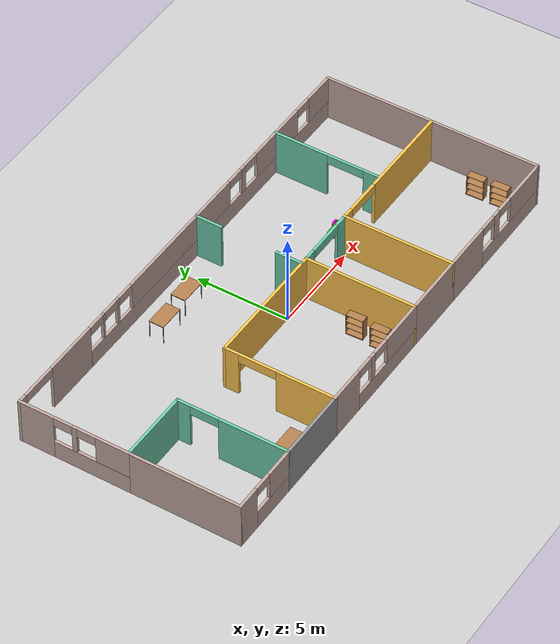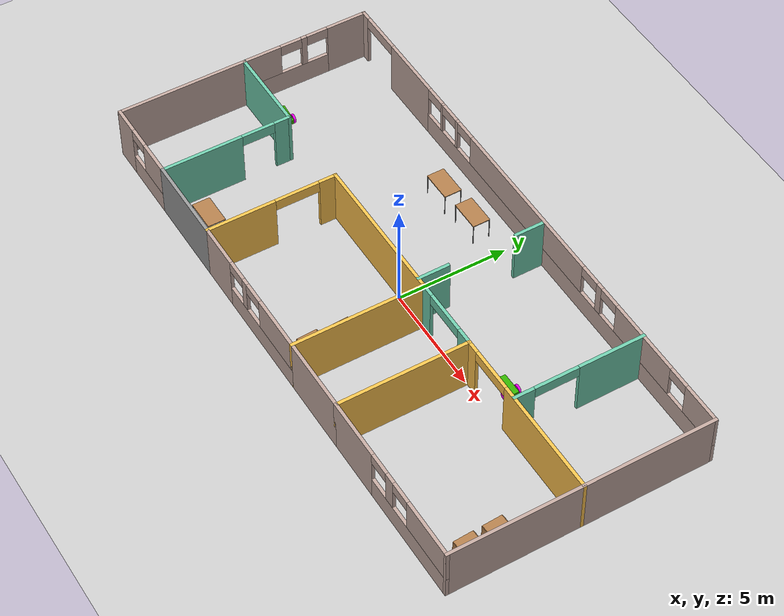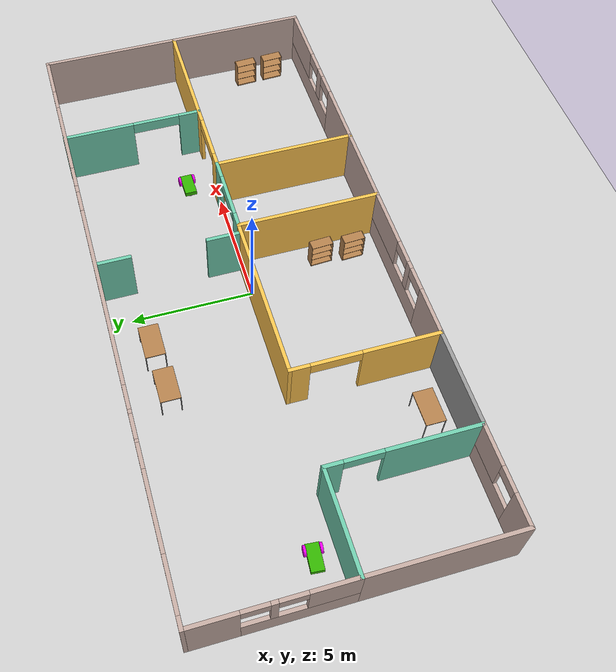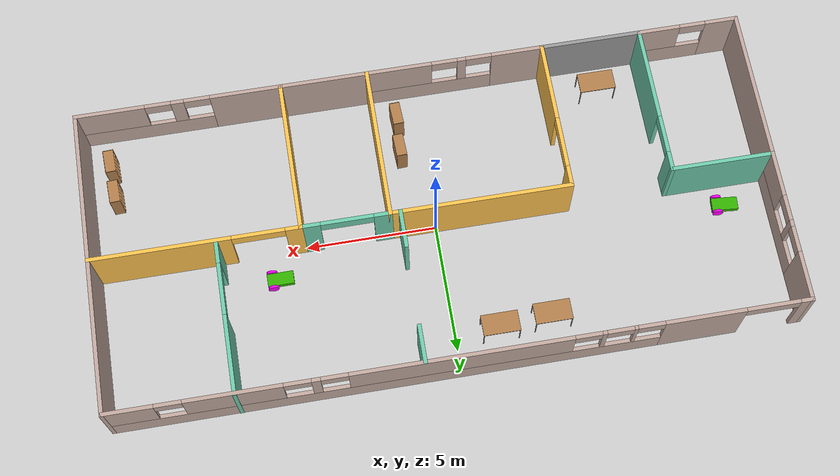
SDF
<sdf version="1.6">
 <world name="default">
  <plugin name="hello" filename="libhello.so"/>
  <light name="sun" type="directional">
   <pose>0 0 10 0 -0 0</pose>
   <diffuse>0.8 0.8 0.8 1</diffuse>
   <specular>0.1 0.1 0.1 1</specular>
   <attenuation>
    <range>1000</range>
    <constant>0.9</constant>
    <linear>0.01</linear>
    <quadratic>0.001</quadratic>
   </attenuation>
   <direction>-0.5 0.5 -1</direction>
  </light>
  <model name="ground_plane">
   <static>1</static>
   <link name="link">
    <collision name="collision">
     <geometry><plane><normal>0 0 1</normal><size>100 100</size></plane></geometry>
     <surface><friction><ode><mu>100</mu><mu2>50</mu2></ode></friction></surface>
    </collision>
    <visual name="visual">
     <cast_shadows>0</cast_shadows>
     <geometry><plane><normal>0 0 1</normal><size>100 100</size></plane></geometry>
     <material>
      <script><uri>file://media/materials/scripts/gazebo.material</uri><name>Gazebo/Grey</name></script>
     </material>
    </visual>
   </link>
  </model>
  <gravity>0 0 -9.8</gravity>
  <magnetic_field>6e-06 2.3e-05 -4.2e-05</magnetic_field>
  <atmosphere type="adiabatic"/>
  <physics name="default_physics" default="0" type="ode">
   <max_step_size>0.001</max_step_size>
   <real_time_factor>1</real_time_factor>
   <real_time_update_rate>1000</real_time_update_rate>
  </physics>
  <scene><ambient>0.4 0.4 0.4 1</ambient><background>0.7 0.7 0.7 1</background><shadows>1</shadows></scene>
  <spherical_coordinates>
   <surface_model>EARTH_WGS84</surface_model>
   <latitude_deg>0</latitude_deg>
   <longitude_deg>0</longitude_deg>
   <elevation>0</elevation>
   <heading_deg>0</heading_deg>
  </spherical_coordinates>
  <model name="Building">
   <pose>0.0388 0.08075 0 0 -0 0</pose>
   <link name="Wall_0">
    <pose>-12.8748 2.91767 0 0 0 -1.5708</pose>
    <visual name="Wall_0_Visual_0">
     <pose>-2.03434 0 1.25 0 -0 0</pose>
     <geometry><box><size>1.93132 0.15 2.5</size></box></geometry>
     <material>
      <script><uri>file://media/materials/scripts/gazebo.material</uri><name>Gazebo/Grey</name></script>
      <ambient>0.760784 0.662745 0.627451 1</ambient>
     </material>
    </visual>
    <collision name="Wall_0_Collision_0">
     <geometry><box><size>1.93132 0.15 2.5</size></box></geometry>
     <pose>-2.03434 0 1.25 0 -0 0</pose>
    </collision>
    <visual name="Wall_0_Visual_1">
     <pose>0.965658 0 0.5 0 -0 0</pose>
     <geometry><box><size>4.06868 0.15 1</size></box></geometry>
     <material>
      <script><uri>file://media/materials/scripts/gazebo.material</uri><name>Gazebo/Grey</name></script>
      <ambient>0.760784 0.662745 0.627451 1</ambient>
     </material>
    </visual>
    <collision name="Wall_0_Collision_1">
     <geometry><box><size>4.06868 0.15 1</size></box></geometry>
     <pose>0.965658 0 0.5 0 -0 0</pose>
    </collision>
    <visual name="Wall_0_Visual_2">
     <pose>0.061576 0 1.75 0 -0 0</pose>
     <geometry><box><size>0.26052 0.15 1.5</size></box></geometry>
     <material>
      <script><uri>file://media/materials/scripts/gazebo.material</uri><name>Gazebo/Grey</name></script>
      <ambient>0.760784 0.662745 0.627451 1</ambient>
     </material>
    </visual>
    <collision name="Wall_0_Collision_2">
     <geometry><box><size>0.26052 0.15 1.5</size></box></geometry>
     <pose>0.061576 0 1.75 0 -0 0</pose>
    </collision>
    <visual name="Wall_0_Visual_3">
     <pose>2.09592 0 1.75 0 -0 0</pose>
     <geometry><box><size>1.80816 0.15 1.5</size></box></geometry>
     <material>
      <script><uri>file://media/materials/scripts/gazebo.material</uri><name>Gazebo/Grey</name></script>
      <ambient>0.760784 0.662745 0.627451 1</ambient>
     </material>
    </visual>
    <collision name="Wall_0_Collision_3">
     <geometry><box><size>1.80816 0.15 1.5</size></box></geometry>
     <pose>2.09592 0 1.75 0 -0 0</pose>
    </collision>
    <visual name="Wall_0_Visual_4">
     <pose>-0.568684 0 2.25 0 -0 0</pose>
     <geometry><box><size>1 0.15 0.5</size></box></geometry>
     <material>
      <script><uri>file://media/materials/scripts/gazebo.material</uri><name>Gazebo/Grey</name></script>
      <ambient>0.760784 0.662745 0.627451 1</ambient>
     </material>
    </visual>
    <collision name="Wall_0_Collision_4">
     <geometry><box><size>1 0.15 0.5</size></box></geometry>
     <pose>-0.568684 0 2.25 0 -0 0</pose>
    </collision>
    <visual name="Wall_0_Visual_5">
     <pose>0.691837 0 2.25 0 -0 0</pose>
     <geometry><box><size>1 0.15 0.5</size></box></geometry>
     <material>
      <script><uri>file://media/materials/scripts/gazebo.material</uri><name>Gazebo/Grey</name></script>
      <ambient>0.760784 0.662745 0.627451 1</ambient>
     </material>
    </visual>
    <collision name="Wall_0_Collision_5">
     <geometry><box><size>1 0.15 0.5</size></box></geometry>
     <pose>0.691837 0 2.25 0 -0 0</pose>
    </collision>
   </link>
   <link name="Wall_10">
    <collision name="Wall_10_Collision">
     <geometry><box><size>4 0.15 2.5</size></box></geometry>
     <pose>0 0 1.25 0 -0 0</pose>
    </collision>
    <visual name="Wall_10_Visual">
     <pose>0 0 1.25 0 -0 0</pose>
     <geometry><box><size>4 0.15 2.5</size></box></geometry>
     <material>
      <script><uri>file://media/materials/scripts/gazebo.material</uri><name>Gazebo/Grey</name></script>
      <ambient>1 1 1 1</ambient>
     </material>
    </visual>
    <pose>-7.1 -5.85736 0 0 0 -1.2e-05</pose>
   </link>
   <link name="Wall_12">
    <pose>-5.175 -2.93236 0 0 -0 1.57074</pose>
    <visual name="Wall_12_Visual_0">
     <pose>-1.42698 0 1.25 0 -0 0</pose>
     <geometry><box><size>3.14604 0.15 2.5</size></box></geometry>
     <material>
      <script><uri>file://media/materials/scripts/gazebo.material</uri><name>Gazebo/Grey</name></script>
      <ambient>1 0.764706 0.305882 1</ambient>
     </material>
    </visual>
    <collision name="Wall_12_Collision_0">
     <geometry><box><size>3.14604 0.15 2.5</size></box></geometry>
     <pose>-1.42698 0 1.25 0 -0 0</pose>
    </collision>
    <visual name="Wall_12_Visual_1">
     <pose>2.57302 0 1.25 0 -0 0</pose>
     <geometry><box><size>0.853958 0.15 2.5</size></box></geometry>
     <material>
      <script><uri>file://media/materials/scripts/gazebo.material</uri><name>Gazebo/Grey</name></script>
      <ambient>1 0.764706 0.305882 1</ambient>
     </material>
    </visual>
    <collision name="Wall_12_Collision_1">
     <geometry><box><size>0.853958 0.15 2.5</size></box></geometry>
     <pose>2.57302 0 1.25 0 -0 0</pose>
    </collision>
    <visual name="Wall_12_Visual_2">
     <pose>1.14604 0 2.25 0 -0 0</pose>
     <geometry><box><size>2 0.15 0.5</size></box></geometry>
     <material>
      <script><uri>file://media/materials/scripts/gazebo.material</uri><name>Gazebo/Grey</name></script>
      <ambient>1 0.764706 0.305882 1</ambient>
     </material>
    </visual>
    <collision name="Wall_12_Collision_2">
     <geometry><box><size>2 0.15 0.5</size></box></geometry>
     <pose>1.14604 0 2.25 0 -0 0</pose>
    </collision>
   </link>
   <link name="Wall_14">
    <pose>-1.75018 -5.85738 0 0 -0 0</pose>
    <visual name="Wall_14_Visual_0">
     <pose>-2.46755 0 1.25 0 -0 0</pose>
     <geometry><box><size>2.0649 0.15 2.5</size></box></geometry>
     <material>
      <script><uri>file://media/materials/scripts/gazebo.material</uri><name>Gazebo/Grey</name></script>
      <ambient>0.760784 0.662745 0.627451 1</ambient>
     </material>
    </visual>
    <collision name="Wall_14_Collision_0">
     <geometry><box><size>2.0649 0.15 2.5</size></box></geometry>
     <pose>-2.46755 0 1.25 0 -0 0</pose>
    </collision>
    <visual name="Wall_14_Visual_1">
     <pose>1.03245 0 0.5 0 -0 0</pose>
     <geometry><box><size>4.93509 0.15 1</size></box></geometry>
     <material>
      <script><uri>file://media/materials/scripts/gazebo.material</uri><name>Gazebo/Grey</name></script>
      <ambient>0.760784 0.662745 0.627451 1</ambient>
     </material>
    </visual>
    <collision name="Wall_14_Collision_1">
     <geometry><box><size>4.93509 0.15 1</size></box></geometry>
     <pose>1.03245 0 0.5 0 -0 0</pose>
    </collision>
    <visual name="Wall_14_Visual_2">
     <pose>-0.267578 0 1.75 0 -0 0</pose>
     <geometry><box><size>0.335034 0.15 1.5</size></box></geometry>
     <material>
      <script><uri>file://media/materials/scripts/gazebo.material</uri><name>Gazebo/Grey</name></script>
      <ambient>0.760784 0.662745 0.627451 1</ambient>
     </material>
    </visual>
    <collision name="Wall_14_Collision_2">
     <geometry><box><size>0.335034 0.15 1.5</size></box></geometry>
     <pose>-0.267578 0 1.75 0 -0 0</pose>
    </collision>
    <visual name="Wall_14_Visual_3">
     <pose>2.19997 0 1.75 0 -0 0</pose>
     <geometry><box><size>2.60006 0.15 1.5</size></box></geometry>
     <material>
      <script><uri>file://media/materials/scripts/gazebo.material</uri><name>Gazebo/Grey</name></script>
      <ambient>0.760784 0.662745 0.627451 1</ambient>
     </material>
    </visual>
    <collision name="Wall_14_Collision_3">
     <geometry><box><size>2.60006 0.15 1.5</size></box></geometry>
     <pose>2.19997 0 1.75 0 -0 0</pose>
    </collision>
    <visual name="Wall_14_Visual_4">
     <pose>-0.935095 0 2.25 0 -0 0</pose>
     <geometry><box><size>1 0.15 0.5</size></box></geometry>
     <material>
      <script><uri>file://media/materials/scripts/gazebo.material</uri><name>Gazebo/Grey</name></script>
      <ambient>0.760784 0.662745 0.627451 1</ambient>
     </material>
    </visual>
    <collision name="Wall_14_Collision_4">
     <geometry><box><size>1 0.15 0.5</size></box></geometry>
     <pose>-0.935095 0 2.25 0 -0 0</pose>
    </collision>
    <visual name="Wall_14_Visual_5">
     <pose>0.399939 0 2.25 0 -0 0</pose>
     <geometry><box><size>1 0.15 0.5</size></box></geometry>
     <material>
      <script><uri>file://media/materials/scripts/gazebo.material</uri><name>Gazebo/Grey</name></script>
      <ambient>0.760784 0.662745 0.627451 1</ambient>
     </material>
    </visual>
    <collision name="Wall_14_Collision_5">
     <geometry><box><size>1 0.15 0.5</size></box></geometry>
     <pose>0.399939 0 2.25 0 -0 0</pose>
    </collision>
   </link>
   <link name="Wall_16">
    <collision name="Wall_16_Collision">
     <geometry><box><size>6 0.15 2.5</size></box></geometry>
     <pose>0 0 1.25 0 -0 0</pose>
    </collision>
    <visual name="Wall_16_Visual">
     <pose>0 0 1.25 0 -0 0</pose>
     <geometry><box><size>6 0.15 2.5</size></box></geometry>
     <material>
      <script><uri>file://media/materials/scripts/gazebo.material</uri><name>Gazebo/Grey</name></script>
      <ambient>1 0.764706 0.305882 1</ambient>
     </material>
    </visual>
    <pose>1.67482 -2.93238 0 0 -0 1.5708</pose>
   </link>
   <link name="Wall_18">
    <collision name="Wall_18_Collision">
     <geometry><box><size>7 0.15 2.5</size></box></geometry>
     <pose>0 0 1.25 0 -0 0</pose>
    </collision>
    <visual name="Wall_18_Visual">
     <pose>0 0 1.25 0 -0 0</pose>
     <geometry><box><size>7 0.15 2.5</size></box></geometry>
     <material>
      <script><uri>file://media/materials/scripts/gazebo.material</uri><name>Gazebo/Grey</name></script>
      <ambient>1 0.764706 0.305882 1</ambient>
     </material>
    </visual>
    <pose>-1.75 -0.007356 0 0 0 -7e-06</pose>
   </link>
   <link name="Wall_2">
    <collision name="Wall_2_Collision">
     <geometry><box><size>6 0.15 2.5</size></box></geometry>
     <pose>0 0 1.25 0 -0 0</pose>
    </collision>
    <visual name="Wall_2_Visual">
     <pose>0 0 1.25 0 -0 0</pose>
     <geometry><box><size>6 0.15 2.5</size></box></geometry>
     <material>
      <script><uri>file://media/materials/scripts/gazebo.material</uri><name>Gazebo/Grey</name></script>
      <ambient>0.760784 0.662745 0.627451 1</ambient>
     </material>
    </visual>
    <pose>-12.8748 -2.93233 0 0 0 -1.5708</pose>
   </link>
   <link name="Wall_20">
    <pose>3.34982 -0.007379 0 0 -0 0</pose>
    <visual name="Wall_20_Visual_0">
     <pose>-1.403 0 1.25 0 -0 0</pose>
     <geometry><box><size>0.693999 0.15 2.5</size></box></geometry>
     <material>
      <script><uri>file://media/materials/scripts/gazebo.material</uri><name>Gazebo/Grey</name></script>
      <ambient>0.435294 0.796078 0.67451 1</ambient>
     </material>
    </visual>
    <collision name="Wall_20_Collision_0">
     <geometry><box><size>0.693999 0.15 2.5</size></box></geometry>
     <pose>-1.403 0 1.25 0 -0 0</pose>
    </collision>
    <visual name="Wall_20_Visual_1">
     <pose>1.347 0 1.25 0 -0 0</pose>
     <geometry><box><size>0.806001 0.15 2.5</size></box></geometry>
     <material>
      <script><uri>file://media/materials/scripts/gazebo.material</uri><name>Gazebo/Grey</name></script>
      <ambient>0.435294 0.796078 0.67451 1</ambient>
     </material>
    </visual>
    <collision name="Wall_20_Collision_1">
     <geometry><box><size>0.806001 0.15 2.5</size></box></geometry>
     <pose>1.347 0 1.25 0 -0 0</pose>
    </collision>
    <visual name="Wall_20_Visual_2">
     <pose>-0.056001 0 2.25 0 -0 0</pose>
     <geometry><box><size>2 0.15 0.5</size></box></geometry>
     <material>
      <script><uri>file://media/materials/scripts/gazebo.material</uri><name>Gazebo/Grey</name></script>
      <ambient>0.435294 0.796078 0.67451 1</ambient>
     </material>
    </visual>
    <collision name="Wall_20_Collision_2">
     <geometry><box><size>2 0.15 0.5</size></box></geometry>
     <pose>-0.056001 0 2.25 0 -0 0</pose>
    </collision>
   </link>
   <link name="Wall_23">
    <collision name="Wall_23_Collision">
     <geometry><box><size>3.5 0.15 2.5</size></box></geometry>
     <pose>0 0 1.25 0 -0 0</pose>
    </collision>
    <visual name="Wall_23_Visual">
     <pose>0 0 1.25 0 -0 0</pose>
     <geometry><box><size>3.5 0.15 2.5</size></box></geometry>
     <material>
      <script><uri>file://media/materials/scripts/gazebo.material</uri><name>Gazebo/Grey</name></script>
      <ambient>0.760784 0.662745 0.627451 1</ambient>
     </material>
    </visual>
    <pose>3.34982 -5.85738 0 0 -0 0</pose>
   </link>
   <link name="Wall_24">
    <collision name="Wall_24_Collision">
     <geometry><box><size>6 0.15 2.5</size></box></geometry>
     <pose>0 0 1.25 0 -0 0</pose>
    </collision>
    <visual name="Wall_24_Visual">
     <pose>0 0 1.25 0 -0 0</pose>
     <geometry><box><size>6 0.15 2.5</size></box></geometry>
     <material>
      <script><uri>file://media/materials/scripts/gazebo.material</uri><name>Gazebo/Grey</name></script>
      <ambient>1 0.764706 0.305882 1</ambient>
     </material>
    </visual>
    <pose>5.02482 -2.93238 0 0 -0 1.5708</pose>
   </link>
   <link name="Wall_29">
    <pose>8.94982 -5.85738 0 0 -0 0</pose>
    <visual name="Wall_29_Visual_0">
     <pose>-2.60604 0 1.25 0 -0 0</pose>
     <geometry><box><size>2.78791 0.15 2.5</size></box></geometry>
     <material>
      <script><uri>file://media/materials/scripts/gazebo.material</uri><name>Gazebo/Grey</name></script>
      <ambient>0.760784 0.662745 0.627451 1</ambient>
     </material>
    </visual>
    <collision name="Wall_29_Collision_0">
     <geometry><box><size>2.78791 0.15 2.5</size></box></geometry>
     <pose>-2.60604 0 1.25 0 -0 0</pose>
    </collision>
    <visual name="Wall_29_Visual_1">
     <pose>1.39396 0 0.5 0 -0 0</pose>
     <geometry><box><size>5.21209 0.15 1</size></box></geometry>
     <material>
      <script><uri>file://media/materials/scripts/gazebo.material</uri><name>Gazebo/Grey</name></script>
      <ambient>0.760784 0.662745 0.627451 1</ambient>
     </material>
    </visual>
    <collision name="Wall_29_Collision_1">
     <geometry><box><size>5.21209 0.15 1</size></box></geometry>
     <pose>1.39396 0 0.5 0 -0 0</pose>
    </collision>
    <visual name="Wall_29_Visual_2">
     <pose>0.036339 0 1.75 0 -0 0</pose>
     <geometry><box><size>0.496857 0.15 1.5</size></box></geometry>
     <material>
      <script><uri>file://media/materials/scripts/gazebo.material</uri><name>Gazebo/Grey</name></script>
      <ambient>0.760784 0.662745 0.627451 1</ambient>
     </material>
    </visual>
    <collision name="Wall_29_Collision_2">
     <geometry><box><size>0.496857 0.15 1.5</size></box></geometry>
     <pose>0.036339 0 1.75 0 -0 0</pose>
    </collision>
    <visual name="Wall_29_Visual_3">
     <pose>2.64238 0 1.75 0 -0 0</pose>
     <geometry><box><size>2.71523 0.15 1.5</size></box></geometry>
     <material>
      <script><uri>file://media/materials/scripts/gazebo.material</uri><name>Gazebo/Grey</name></script>
      <ambient>0.760784 0.662745 0.627451 1</ambient>
     </material>
    </visual>
    <collision name="Wall_29_Collision_3">
     <geometry><box><size>2.71523 0.15 1.5</size></box></geometry>
     <pose>2.64238 0 1.75 0 -0 0</pose>
    </collision>
    <visual name="Wall_29_Visual_4">
     <pose>-0.71209 0 2.25 0 -0 0</pose>
     <geometry><box><size>1 0.15 0.5</size></box></geometry>
     <material>
      <script><uri>file://media/materials/scripts/gazebo.material</uri><name>Gazebo/Grey</name></script>
      <ambient>0.760784 0.662745 0.627451 1</ambient>
     </material>
    </visual>
    <collision name="Wall_29_Collision_4">
     <geometry><box><size>1 0.15 0.5</size></box></geometry>
     <pose>-0.71209 0 2.25 0 -0 0</pose>
    </collision>
    <visual name="Wall_29_Visual_5">
     <pose>0.784767 0 2.25 0 -0 0</pose>
     <geometry><box><size>1 0.15 0.5</size></box></geometry>
     <material>
      <script><uri>file://media/materials/scripts/gazebo.material</uri><name>Gazebo/Grey</name></script>
      <ambient>0.760784 0.662745 0.627451 1</ambient>
     </material>
    </visual>
    <collision name="Wall_29_Collision_5">
     <geometry><box><size>1 0.15 0.5</size></box></geometry>
     <pose>0.784767 0 2.25 0 -0 0</pose>
    </collision>
   </link>
   <link name="Wall_31">
    <collision name="Wall_31_Collision">
     <geometry><box><size>6 0.15 2.5</size></box></geometry>
     <pose>0 0 1.25 0 -0 0</pose>
    </collision>
    <visual name="Wall_31_Visual">
     <pose>0 0 1.25 0 -0 0</pose>
     <geometry><box><size>6 0.15 2.5</size></box></geometry>
     <material>
      <script><uri>file://media/materials/scripts/gazebo.material</uri><name>Gazebo/Grey</name></script>
      <ambient>0.760784 0.662745 0.627451 1</ambient>
     </material>
    </visual>
    <pose>12.8748 -2.93238 0 0 -0 1.5708</pose>
   </link>
   <link name="Wall_33">
    <pose>8.94982 -0.007379 0 0 -0 3.14159</pose>
    <visual name="Wall_33_Visual_0">
     <pose>-1.3254 0 1.25 0 -0 0</pose>
     <geometry><box><size>5.3492 0.15 2.5</size></box></geometry>
     <material>
      <script><uri>file://media/materials/scripts/gazebo.material</uri><name>Gazebo/Grey</name></script>
      <ambient>1 0.764706 0.305882 1</ambient>
     </material>
    </visual>
    <collision name="Wall_33_Collision_0">
     <geometry><box><size>5.3492 0.15 2.5</size></box></geometry>
     <pose>-1.3254 0 1.25 0 -0 0</pose>
    </collision>
    <visual name="Wall_33_Visual_1">
     <pose>3.6746 0 1.25 0 -0 0</pose>
     <geometry><box><size>0.650803 0.15 2.5</size></box></geometry>
     <material>
      <script><uri>file://media/materials/scripts/gazebo.material</uri><name>Gazebo/Grey</name></script>
      <ambient>1 0.764706 0.305882 1</ambient>
     </material>
    </visual>
    <collision name="Wall_33_Collision_1">
     <geometry><box><size>0.650803 0.15 2.5</size></box></geometry>
     <pose>3.6746 0 1.25 0 -0 0</pose>
    </collision>
    <visual name="Wall_33_Visual_2">
     <pose>2.3492 0 2.25 0 -0 0</pose>
     <geometry><box><size>2 0.15 0.5</size></box></geometry>
     <material>
      <script><uri>file://media/materials/scripts/gazebo.material</uri><name>Gazebo/Grey</name></script>
      <ambient>1 0.764706 0.305882 1</ambient>
     </material>
    </visual>
    <collision name="Wall_33_Collision_2">
     <geometry><box><size>2 0.15 0.5</size></box></geometry>
     <pose>2.3492 0 2.25 0 -0 0</pose>
    </collision>
   </link>
   <link name="Wall_37">
    <collision name="Wall_37_Collision">
     <geometry><box><size>6 0.15 2.5</size></box></geometry>
     <pose>0 0 1.25 0 -0 0</pose>
    </collision>
    <visual name="Wall_37_Visual">
     <pose>0 0 1.25 0 -0 0</pose>
     <geometry><box><size>6 0.15 2.5</size></box></geometry>
     <material>
      <script><uri>file://media/materials/scripts/gazebo.material</uri><name>Gazebo/Grey</name></script>
      <ambient>0.760784 0.662745 0.627451 1</ambient>
     </material>
    </visual>
    <pose>12.8748 2.91762 0 0 -0 1.5708</pose>
   </link>
   <link name="Wall_39">
    <pose>0 5.84264 0 0 0 -2e-06</pose>
    <visual name="Wall_39_Visual_0">
     <pose>-12.6963 0 1.25 0 -0 0</pose>
     <geometry><box><size>0.507003 0.15 2.5</size></box></geometry>
     <material>
      <script><uri>file://media/materials/scripts/gazebo.material</uri><name>Gazebo/Grey</name></script>
      <ambient>0.760784 0.662745 0.627451 1</ambient>
     </material>
    </visual>
    <collision name="Wall_39_Collision_0">
     <geometry><box><size>0.507003 0.15 2.5</size></box></geometry>
     <pose>-12.6963 0 1.25 0 -0 0</pose>
    </collision>
    <visual name="Wall_39_Visual_1">
     <pose>-8.93538 0 1.25 0 -0 0</pose>
     <geometry><box><size>3.01488 0.15 2.5</size></box></geometry>
     <material>
      <script><uri>file://media/materials/scripts/gazebo.material</uri><name>Gazebo/Grey</name></script>
      <ambient>0.760784 0.662745 0.627451 1</ambient>
     </material>
    </visual>
    <collision name="Wall_39_Collision_1">
     <geometry><box><size>3.01488 0.15 2.5</size></box></geometry>
     <pose>-8.93538 0 1.25 0 -0 0</pose>
    </collision>
    <visual name="Wall_39_Visual_2">
     <pose>2.76094 0 0.5 0 -0 0</pose>
     <geometry><box><size>20.3778 0.15 1</size></box></geometry>
     <material>
      <script><uri>file://media/materials/scripts/gazebo.material</uri><name>Gazebo/Grey</name></script>
      <ambient>0.760784 0.662745 0.627451 1</ambient>
     </material>
    </visual>
    <collision name="Wall_39_Collision_2">
     <geometry><box><size>20.3778 0.15 1</size></box></geometry>
     <pose>2.76094 0 0.5 0 -0 0</pose>
    </collision>
    <visual name="Wall_39_Visual_3">
     <pose>-6.3614 0 1.75 0 -0 0</pose>
     <geometry><box><size>0.133081 0.15 1.5</size></box></geometry>
     <material>
      <script><uri>file://media/materials/scripts/gazebo.material</uri><name>Gazebo/Grey</name></script>
      <ambient>0.760784 0.662745 0.627451 1</ambient>
     </material>
    </visual>
    <collision name="Wall_39_Collision_3">
     <geometry><box><size>0.133081 0.15 1.5</size></box></geometry>
     <pose>-6.3614 0 1.75 0 -0 0</pose>
    </collision>
    <visual name="Wall_39_Visual_4">
     <pose>-5.20894 0 1.75 0 -0 0</pose>
     <geometry><box><size>0.171834 0.15 1.5</size></box></geometry>
     <material>
      <script><uri>file://media/materials/scripts/gazebo.material</uri><name>Gazebo/Grey</name></script>
      <ambient>0.760784 0.662745 0.627451 1</ambient>
     </material>
    </visual>
    <collision name="Wall_39_Collision_4">
     <geometry><box><size>0.171834 0.15 1.5</size></box></geometry>
     <pose>-5.20894 0 1.75 0 -0 0</pose>
    </collision>
    <visual name="Wall_39_Visual_5">
     <pose>-0.013145 0 1.75 0 -0 0</pose>
     <geometry><box><size>8.21975 0.15 1.5</size></box></geometry>
     <material>
      <script><uri>file://media/materials/scripts/gazebo.material</uri><name>Gazebo/Grey</name></script>
      <ambient>0.760784 0.662745 0.627451 1</ambient>
     </material>
    </visual>
    <collision name="Wall_39_Collision_5">
     <geometry><box><size>8.21975 0.15 1.5</size></box></geometry>
     <pose>-0.013145 0 1.75 0 -0 0</pose>
    </collision>
    <visual name="Wall_39_Visual_6">
     <pose>5.26425 0 1.75 0 -0 0</pose>
     <geometry><box><size>0.335033 0.15 1.5</size></box></geometry>
     <material>
      <script><uri>file://media/materials/scripts/gazebo.material</uri><name>Gazebo/Grey</name></script>
      <ambient>0.760784 0.662745 0.627451 1</ambient>
     </material>
    </visual>
    <collision name="Wall_39_Collision_6">
     <geometry><box><size>0.335033 0.15 1.5</size></box></geometry>
     <pose>5.26425 0 1.75 0 -0 0</pose>
    </collision>
    <visual name="Wall_39_Visual_7">
     <pose>8.23773 0 1.75 0 -0 0</pose>
     <geometry><box><size>3.61194 0.15 1.5</size></box></geometry>
     <material>
      <script><uri>file://media/materials/scripts/gazebo.material</uri><name>Gazebo/Grey</name></script>
      <ambient>0.760784 0.662745 0.627451 1</ambient>
     </material>
    </visual>
    <collision name="Wall_39_Collision_7">
     <geometry><box><size>3.61194 0.15 1.5</size></box></geometry>
     <pose>8.23773 0 1.75 0 -0 0</pose>
    </collision>
    <visual name="Wall_39_Visual_8">
     <pose>11.9968 0 1.75 0 -0 0</pose>
     <geometry><box><size>1.90612 0.15 1.5</size></box></geometry>
     <material>
      <script><uri>file://media/materials/scripts/gazebo.material</uri><name>Gazebo/Grey</name></script>
      <ambient>0.760784 0.662745 0.627451 1</ambient>
     </material>
    </visual>
    <collision name="Wall_39_Collision_8">
     <geometry><box><size>1.90612 0.15 1.5</size></box></geometry>
     <pose>11.9968 0 1.75 0 -0 0</pose>
    </collision>
    <visual name="Wall_39_Visual_9">
     <pose>-11.4428 0 2.25 0 -0 0</pose>
     <geometry><box><size>2 0.15 0.5</size></box></geometry>
     <material>
      <script><uri>file://media/materials/scripts/gazebo.material</uri><name>Gazebo/Grey</name></script>
      <ambient>0.760784 0.662745 0.627451 1</ambient>
     </material>
    </visual>
    <collision name="Wall_39_Collision_9">
     <geometry><box><size>2 0.15 0.5</size></box></geometry>
     <pose>-11.4428 0 2.25 0 -0 0</pose>
    </collision>
    <visual name="Wall_39_Visual_10">
     <pose>-6.92794 0 2.25 0 -0 0</pose>
     <geometry><box><size>1 0.15 0.5</size></box></geometry>
     <material>
      <script><uri>file://media/materials/scripts/gazebo.material</uri><name>Gazebo/Grey</name></script>
      <ambient>0.760784 0.662745 0.627451 1</ambient>
     </material>
    </visual>
    <collision name="Wall_39_Collision_10">
     <geometry><box><size>1 0.15 0.5</size></box></geometry>
     <pose>-6.92794 0 2.25 0 -0 0</pose>
    </collision>
    <visual name="Wall_39_Visual_11">
     <pose>-5.79486 0 2.25 0 -0 0</pose>
     <geometry><box><size>1 0.15 0.5</size></box></geometry>
     <material>
      <script><uri>file://media/materials/scripts/gazebo.material</uri><name>Gazebo/Grey</name></script>
      <ambient>0.760784 0.662745 0.627451 1</ambient>
     </material>
    </visual>
    <collision name="Wall_39_Collision_11">
     <geometry><box><size>1 0.15 0.5</size></box></geometry>
     <pose>-5.79486 0 2.25 0 -0 0</pose>
    </collision>
    <visual name="Wall_39_Visual_12">
     <pose>-4.62302 0 2.25 0 -0 0</pose>
     <geometry><box><size>1 0.15 0.5</size></box></geometry>
     <material>
      <script><uri>file://media/materials/scripts/gazebo.material</uri><name>Gazebo/Grey</name></script>
      <ambient>0.760784 0.662745 0.627451 1</ambient>
     </material>
    </visual>
    <collision name="Wall_39_Collision_12">
     <geometry><box><size>1 0.15 0.5</size></box></geometry>
     <pose>-4.62302 0 2.25 0 -0 0</pose>
    </collision>
    <visual name="Wall_39_Visual_13">
     <pose>4.59673 0 2.25 0 -0 0</pose>
     <geometry><box><size>1 0.15 0.5</size></box></geometry>
     <material>
      <script><uri>file://media/materials/scripts/gazebo.material</uri><name>Gazebo/Grey</name></script>
      <ambient>0.760784 0.662745 0.627451 1</ambient>
     </material>
    </visual>
    <collision name="Wall_39_Collision_13">
     <geometry><box><size>1 0.15 0.5</size></box></geometry>
     <pose>4.59673 0 2.25 0 -0 0</pose>
    </collision>
    <visual name="Wall_39_Visual_14">
     <pose>5.93177 0 2.25 0 -0 0</pose>
     <geometry><box><size>1 0.15 0.5</size></box></geometry>
     <material>
      <script><uri>file://media/materials/scripts/gazebo.material</uri><name>Gazebo/Grey</name></script>
      <ambient>0.760784 0.662745 0.627451 1</ambient>
     </material>
    </visual>
    <collision name="Wall_39_Collision_14">
     <geometry><box><size>1 0.15 0.5</size></box></geometry>
     <pose>5.93177 0 2.25 0 -0 0</pose>
    </collision>
    <visual name="Wall_39_Visual_15">
     <pose>10.5437 0 2.25 0 -0 0</pose>
     <geometry><box><size>1 0.15 0.5</size></box></geometry>
     <material>
      <script><uri>file://media/materials/scripts/gazebo.material</uri><name>Gazebo/Grey</name></script>
      <ambient>0.760784 0.662745 0.627451 1</ambient>
     </material>
    </visual>
    <collision name="Wall_39_Collision_15">
     <geometry><box><size>1 0.15 0.5</size></box></geometry>
     <pose>10.5437 0 2.25 0 -0 0</pose>
    </collision>
   </link>
   <link name="Wall_4">
    <pose>-10.9498 -5.85733 0 0 -0 0</pose>
    <visual name="Wall_4_Visual_0">
     <pose>-1.34533 0 1.25 0 -0 0</pose>
     <geometry><box><size>1.30933 0.15 2.5</size></box></geometry>
     <material>
      <script><uri>file://media/materials/scripts/gazebo.material</uri><name>Gazebo/Grey</name></script>
      <ambient>0.760784 0.662745 0.627451 1</ambient>
     </material>
    </visual>
    <collision name="Wall_4_Collision_0">
     <geometry><box><size>1.30933 0.15 2.5</size></box></geometry>
     <pose>-1.34533 0 1.25 0 -0 0</pose>
    </collision>
    <visual name="Wall_4_Visual_1">
     <pose>0.654667 0 0.5 0 -0 0</pose>
     <geometry><box><size>2.69067 0.15 1</size></box></geometry>
     <material>
      <script><uri>file://media/materials/scripts/gazebo.material</uri><name>Gazebo/Grey</name></script>
      <ambient>0.760784 0.662745 0.627451 1</ambient>
     </material>
    </visual>
    <collision name="Wall_4_Collision_1">
     <geometry><box><size>2.69067 0.15 1</size></box></geometry>
     <pose>0.654667 0 0.5 0 -0 0</pose>
    </collision>
    <visual name="Wall_4_Visual_2">
     <pose>1.15467 0 1.75 0 -0 0</pose>
     <geometry><box><size>1.69067 0.15 1.5</size></box></geometry>
     <material>
      <script><uri>file://media/materials/scripts/gazebo.material</uri><name>Gazebo/Grey</name></script>
      <ambient>0.760784 0.662745 0.627451 1</ambient>
     </material>
    </visual>
    <collision name="Wall_4_Collision_2">
     <geometry><box><size>1.69067 0.15 1.5</size></box></geometry>
     <pose>1.15467 0 1.75 0 -0 0</pose>
    </collision>
    <visual name="Wall_4_Visual_3">
     <pose>-0.190666 0 2.25 0 -0 0</pose>
     <geometry><box><size>1 0.15 0.5</size></box></geometry>
     <material>
      <script><uri>file://media/materials/scripts/gazebo.material</uri><name>Gazebo/Grey</name></script>
      <ambient>0.760784 0.662745 0.627451 1</ambient>
     </material>
    </visual>
    <collision name="Wall_4_Collision_3">
     <geometry><box><size>1 0.15 0.5</size></box></geometry>
     <pose>-0.190666 0 2.25 0 -0 0</pose>
    </collision>
   </link>
   <link name="Wall_41">
    <collision name="Wall_41_Collision">
     <geometry><box><size>1.5 0.15 2.5</size></box></geometry>
     <pose>0 0 1.25 0 -0 0</pose>
    </collision>
    <visual name="Wall_41_Visual">
     <pose>0 0 1.25 0 -0 0</pose>
     <geometry><box><size>1.5 0.15 2.5</size></box></geometry>
     <material>
      <script><uri>file://media/materials/scripts/gazebo.material</uri><name>Gazebo/Grey</name></script>
      <ambient>0.435294 0.796078 0.67451 1</ambient>
     </material>
    </visual>
    <pose>1.2911 0.669666 0 0 -0 1.5708</pose>
   </link>
   <link name="Wall_43">
    <collision name="Wall_43_Collision">
     <geometry><box><size>1.5 0.15 2.5</size></box></geometry>
     <pose>0 0 1.25 0 -0 0</pose>
    </collision>
    <visual name="Wall_43_Visual">
     <pose>0 0 1.25 0 -0 0</pose>
     <geometry><box><size>1.5 0.15 2.5</size></box></geometry>
     <material>
      <script><uri>file://media/materials/scripts/gazebo.material</uri><name>Gazebo/Grey</name></script>
      <ambient>0.435294 0.796078 0.67451 1</ambient>
     </material>
    </visual>
    <pose>1.32628 5.15934 0 0 0 -1.5708</pose>
   </link>
   <link name="Wall_45">
    <pose>8.17731 2.93238 0 0 -0 1.5708</pose>
    <visual name="Wall_45_Visual_0">
     <pose>-2.51976 0 1.25 0 -0 0</pose>
     <geometry><box><size>0.960478 0.15 2.5</size></box></geometry>
     <material>
      <script><uri>file://media/materials/scripts/gazebo.material</uri><name>Gazebo/Grey</name></script>
      <ambient>0.435294 0.796078 0.67451 1</ambient>
     </material>
    </visual>
    <collision name="Wall_45_Collision_0">
     <geometry><box><size>0.960478 0.15 2.5</size></box></geometry>
     <pose>-2.51976 0 1.25 0 -0 0</pose>
    </collision>
    <visual name="Wall_45_Visual_1">
     <pose>1.48024 0 1.25 0 -0 0</pose>
     <geometry><box><size>3.03952 0.15 2.5</size></box></geometry>
     <material>
      <script><uri>file://media/materials/scripts/gazebo.material</uri><name>Gazebo/Grey</name></script>
      <ambient>0.435294 0.796078 0.67451 1</ambient>
     </material>
    </visual>
    <collision name="Wall_45_Collision_1">
     <geometry><box><size>3.03952 0.15 2.5</size></box></geometry>
     <pose>1.48024 0 1.25 0 -0 0</pose>
    </collision>
    <visual name="Wall_45_Visual_2">
     <pose>-1.03952 0 2.25 0 -0 0</pose>
     <geometry><box><size>2 0.15 0.5</size></box></geometry>
     <material>
      <script><uri>file://media/materials/scripts/gazebo.material</uri><name>Gazebo/Grey</name></script>
      <ambient>0.435294 0.796078 0.67451 1</ambient>
     </material>
    </visual>
    <collision name="Wall_45_Collision_2">
     <geometry><box><size>2 0.15 0.5</size></box></geometry>
     <pose>-1.03952 0 2.25 0 -0 0</pose>
    </collision>
   </link>
   <link name="Wall_6">
    <pose>-9.02482 -2.93233 0 0 -0 1.5708</pose>
    <visual name="Wall_6_Visual_0">
     <pose>-1.14251 0 1.25 0 -0 0</pose>
     <geometry><box><size>3.71499 0.15 2.5</size></box></geometry>
     <material>
      <script><uri>file://media/materials/scripts/gazebo.material</uri><name>Gazebo/Grey</name></script>
      <ambient>0.435294 0.796078 0.67451 1</ambient>
     </material>
    </visual>
    <collision name="Wall_6_Collision_0">
     <geometry><box><size>3.71499 0.15 2.5</size></box></geometry>
     <pose>-1.14251 0 1.25 0 -0 0</pose>
    </collision>
    <visual name="Wall_6_Visual_1">
     <pose>2.6075 0 1.25 0 -0 0</pose>
     <geometry><box><size>0.78501 0.15 2.5</size></box></geometry>
     <material>
      <script><uri>file://media/materials/scripts/gazebo.material</uri><name>Gazebo/Grey</name></script>
      <ambient>0.435294 0.796078 0.67451 1</ambient>
     </material>
    </visual>
    <collision name="Wall_6_Collision_1">
     <geometry><box><size>0.78501 0.15 2.5</size></box></geometry>
     <pose>2.6075 0 1.25 0 -0 0</pose>
    </collision>
    <visual name="Wall_6_Visual_2">
     <pose>1.46499 0 2.25 0 -0 0</pose>
     <geometry><box><size>1.5 0.15 0.5</size></box></geometry>
     <material>
      <script><uri>file://media/materials/scripts/gazebo.material</uri><name>Gazebo/Grey</name></script>
      <ambient>0.435294 0.796078 0.67451 1</ambient>
     </material>
    </visual>
    <collision name="Wall_6_Collision_2">
     <geometry><box><size>1.5 0.15 0.5</size></box></geometry>
     <pose>1.46499 0 2.25 0 -0 0</pose>
    </collision>
   </link>
   <link name="Wall_8">
    <collision name="Wall_8_Collision">
     <geometry><box><size>4 0.15 2.5</size></box></geometry>
     <pose>0 0 1.25 0 -0 0</pose>
    </collision>
    <visual name="Wall_8_Visual">
     <pose>0 0 1.25 0 -0 0</pose>
     <geometry><box><size>4 0.15 2.5</size></box></geometry>
     <material>
      <script><uri>file://media/materials/scripts/gazebo.material</uri><name>Gazebo/Grey</name></script>
      <ambient>0.435294 0.796078 0.67451 1</ambient>
     </material>
    </visual>
    <pose>-10.9498 -0.007333 0 0 -0 3.14159</pose>
   </link>
   <static>1</static>
  </model>
  <model name="diffrobot">
   <link name="link_0">
    <pose>-0.05 -0 0.025 0 -0 0</pose>
    <inertial>
     <mass>1</mass>
     <inertia>
      <ixx>0.166667</ixx>
      <ixy>0</ixy>
      <ixz>0</ixz>
      <iyy>0.166667</iyy>
      <iyz>0</iyz>
      <izz>0.166667</izz>
     </inertia>
    </inertial>
    <visual name="visual">
     <geometry><box><size>1 0.5 0.2</size></box></geometry>
     <material>
      <lighting>1</lighting>
      <script><uri>file://media/materials/scripts/gazebo.material</uri><name>Gazebo/Grey</name></script>
      <ambient>0.2 0.7 0 1</ambient>
      <diffuse>0.2 0.7 0 1</diffuse>
      <specular>0.2 0.7 0 1</specular>
      <emissive>0.2 0.7 0 1</emissive>
      <shader type="vertex"><normal_map>__default__</normal_map></shader>
     </material>
    </visual>
    <collision name="collision">
     <geometry><box><size>1 0.5 0.2</size></box></geometry>
     <surface>
      <friction>
       <ode><mu>1</mu><mu2>1</mu2><fdir1>0 0 0</fdir1><slip1>0</slip1><slip2>0</slip2></ode>
       <torsional>
        <coefficient>1</coefficient>
        <patch_radius>0</patch_radius>
        <surface_radius>0</surface_radius>
        <use_patch_radius>1</use_patch_radius>
        <ode><slip>0</slip></ode>
       </torsional>
      </friction>
      <bounce><restitution_coefficient>0</restitution_coefficient><threshold>1e+06</threshold></bounce>
      <contact>
       <collide_without_contact>0</collide_without_contact>
       <collide_without_contact_bitmask>1</collide_without_contact_bitmask>
       <collide_bitmask>1</collide_bitmask>
       <ode>
        <soft_cfm>0</soft_cfm>
        <soft_erp>0.2</soft_erp>
        <kp>1e+13</kp>
        <kd>1</kd>
        <max_vel>0.01</max_vel>
        <min_depth>0</min_depth>
       </ode>
       <bullet>
        <split_impulse>1</split_impulse>
        <split_impulse_penetration_threshold>-0.01</split_impulse_penetration_threshold>
        <soft_cfm>0</soft_cfm>
        <soft_erp>0.2</soft_erp>
        <kp>1e+13</kp>
        <kd>1</kd>
       </bullet>
      </contact>
     </surface>
    </collision>
   </link>
   <link name="link_1">
    <pose>0.25 -0.300019 0.025 1.5707 -0 0</pose>
    <inertial>
     <mass>1</mass>
     <inertia><ixx>0.145833</ixx><ixy>0</ixy><ixz>0</ixz><iyy>0.145833</iyy><iyz>0</iyz><izz>0.125</izz></inertia>
    </inertial>
    <visual name="visual">
     <geometry><cylinder><radius>0.2</radius><length>0.1</length></cylinder></geometry>
     <material>
      <lighting>1</lighting>
      <script><uri>file://media/materials/scripts/gazebo.material</uri><name>Gazebo/Grey</name></script>
      <ambient>1 0 1 1</ambient>
      <diffuse>1 0 1 1</diffuse>
      <specular>1 0 1 1</specular>
      <emissive>1 0 1 1</emissive>
      <shader type="vertex"><normal_map>__default__</normal_map></shader>
     </material>
    </visual>
    <collision name="collision">
     <geometry><cylinder><radius>0.2</radius><length>0.1</length></cylinder></geometry>
     <surface>
      <friction>
       <ode><mu>1</mu><mu2>1</mu2><fdir1>0 0 0</fdir1><slip1>0</slip1><slip2>0</slip2></ode>
       <torsional>
        <coefficient>1</coefficient>
        <patch_radius>0</patch_radius>
        <surface_radius>0</surface_radius>
        <use_patch_radius>1</use_patch_radius>
        <ode><slip>0</slip></ode>
       </torsional>
      </friction>
      <bounce><restitution_coefficient>0</restitution_coefficient><threshold>1e+06</threshold></bounce>
      <contact>
       <collide_without_contact>0</collide_without_contact>
       <collide_without_contact_bitmask>1</collide_without_contact_bitmask>
       <collide_bitmask>1</collide_bitmask>
       <ode>
        <soft_cfm>0</soft_cfm>
        <soft_erp>0.2</soft_erp>
        <kp>1e+13</kp>
        <kd>1</kd>
        <max_vel>0.01</max_vel>
        <min_depth>0</min_depth>
       </ode>
       <bullet>
        <split_impulse>1</split_impulse>
        <split_impulse_penetration_threshold>-0.01</split_impulse_penetration_threshold>
        <soft_cfm>0</soft_cfm>
        <soft_erp>0.2</soft_erp>
        <kp>1e+13</kp>
        <kd>1</kd>
       </bullet>
      </contact>
     </surface>
    </collision>
   </link>
   <link name="link_1_clone">
    <pose>0.25 0.300019 0.025 1.5707 -0 0</pose>
    <inertial>
     <mass>1</mass>
     <inertia><ixx>0.145833</ixx><ixy>0</ixy><ixz>0</ixz><iyy>0.145833</iyy><iyz>0</iyz><izz>0.125</izz></inertia>
    </inertial>
    <visual name="visual">
     <geometry><cylinder><radius>0.2</radius><length>0.1</length></cylinder></geometry>
     <material>
      <lighting>1</lighting>
      <script><uri>file://media/materials/scripts/gazebo.material</uri><name>Gazebo/Grey</name></script>
      <ambient>1 0 1 1</ambient>
      <diffuse>1 0 1 1</diffuse>
      <specular>1 0 1 1</specular>
      <emissive>1 0 1 1</emissive>
      <shader type="vertex"><normal_map>__default__</normal_map></shader>
     </material>
    </visual>
    <collision name="collision">
     <geometry><cylinder><radius>0.2</radius><length>0.1</length></cylinder></geometry>
     <surface>
      <friction>
       <ode><mu>1</mu><mu2>1</mu2><fdir1>0 0 0</fdir1><slip1>0</slip1><slip2>0</slip2></ode>
       <torsional>
        <coefficient>1</coefficient>
        <patch_radius>0</patch_radius>
        <surface_radius>0</surface_radius>
        <use_patch_radius>1</use_patch_radius>
        <ode><slip>0</slip></ode>
       </torsional>
      </friction>
      <bounce><restitution_coefficient>0</restitution_coefficient><threshold>1e+06</threshold></bounce>
      <contact>
       <collide_without_contact>0</collide_without_contact>
       <collide_without_contact_bitmask>1</collide_without_contact_bitmask>
       <collide_bitmask>1</collide_bitmask>
       <ode>
        <soft_cfm>0</soft_cfm>
        <soft_erp>0.2</soft_erp>
        <kp>1e+13</kp>
        <kd>1</kd>
        <max_vel>0.01</max_vel>
        <min_depth>0</min_depth>
       </ode>
       <bullet>
        <split_impulse>1</split_impulse>
        <split_impulse_penetration_threshold>-0.01</split_impulse_penetration_threshold>
        <soft_cfm>0</soft_cfm>
        <soft_erp>0.2</soft_erp>
        <kp>1e+13</kp>
        <kd>1</kd>
       </bullet>
      </contact>
     </surface>
    </collision>
   </link>
   <link name="link_2">
    <pose>-0.45 0 -0.075 0 -0 0</pose>
    <inertial>
     <mass>1</mass>
     <inertia><ixx>0.1</ixx><ixy>0</ixy><ixz>0</ixz><iyy>0.1</iyy><iyz>0</iyz><izz>0.1</izz></inertia>
    </inertial>
    <visual name="visual">
     <geometry><sphere><radius>0.1</radius></sphere></geometry>
     <material>
      <lighting>1</lighting>
      <script><uri>file://media/materials/scripts/gazebo.material</uri><name>Gazebo/Grey</name></script>
      <ambient>0.3 0.3 0.3 1</ambient>
      <diffuse>0.7 0.7 0.7 1</diffuse>
      <specular>0.01 0.01 0.01 1</specular>
      <emissive>0 0 0 1</emissive>
      <shader type="vertex"><normal_map>__default__</normal_map></shader>
     </material>
    </visual>
    <collision name="collision">
     <geometry><sphere><radius>0.1</radius></sphere></geometry>
     <surface>
      <friction>
       <ode><mu>1</mu><mu2>1</mu2><fdir1>0 0 0</fdir1><slip1>0</slip1><slip2>0</slip2></ode>
       <torsional>
        <coefficient>1</coefficient>
        <patch_radius>0</patch_radius>
        <surface_radius>0</surface_radius>
        <use_patch_radius>1</use_patch_radius>
        <ode><slip>0</slip></ode>
       </torsional>
      </friction>
      <bounce><restitution_coefficient>0</restitution_coefficient><threshold>1e+06</threshold></bounce>
      <contact>
       <collide_without_contact>0</collide_without_contact>
       <collide_without_contact_bitmask>1</collide_without_contact_bitmask>
       <collide_bitmask>1</collide_bitmask>
       <ode>
        <soft_cfm>0</soft_cfm>
        <soft_erp>0.2</soft_erp>
        <kp>1e+13</kp>
        <kd>1</kd>
        <max_vel>0.01</max_vel>
        <min_depth>0</min_depth>
       </ode>
       <bullet>
        <split_impulse>1</split_impulse>
        <split_impulse_penetration_threshold>-0.01</split_impulse_penetration_threshold>
        <soft_cfm>0</soft_cfm>
        <soft_erp>0.2</soft_erp>
        <kp>1e+13</kp>
        <kd>1</kd>
       </bullet>
      </contact>
     </surface>
    </collision>
   </link>
   <joint name="link_0_JOINT_0" type="revolute">
    <parent>link_0</parent>
    <child>link_1</child>
    <axis>
     <xyz>0 0 1</xyz>
     <use_parent_model_frame>0</use_parent_model_frame>
     <limit>
      <lower>-1.79769e+308</lower>
      <upper>1.79769e+308</upper>
      <effort>-1</effort>
      <velocity>-1</velocity>
     </limit>
     <dynamics>
      <spring_reference>0</spring_reference>
      <spring_stiffness>0</spring_stiffness>
      <damping>0</damping>
      <friction>0</friction>
     </dynamics>
    </axis>
    <physics>
     <ode><limit><cfm>0</cfm><erp>0.2</erp></limit><suspension><cfm>0</cfm><erp>0.2</erp></suspension></ode>
    </physics>
   </joint>
   <joint name="link_0_JOINT_1" type="revolute">
    <parent>link_0</parent>
    <child>link_1_clone</child>
    <axis>
     <xyz>0 0 1</xyz>
     <use_parent_model_frame>0</use_parent_model_frame>
     <limit>
      <lower>-1.79769e+308</lower>
      <upper>1.79769e+308</upper>
      <effort>-1</effort>
      <velocity>-1</velocity>
     </limit>
     <dynamics>
      <spring_reference>0</spring_reference>
      <spring_stiffness>0</spring_stiffness>
      <damping>0</damping>
      <friction>0</friction>
     </dynamics>
    </axis>
    <physics>
     <ode><limit><cfm>0</cfm><erp>0.2</erp></limit><suspension><cfm>0</cfm><erp>0.2</erp></suspension></ode>
    </physics>
   </joint>
   <joint name="link_0_JOINT_2" type="ball">
    <parent>link_0</parent>
    <child>link_2</child>
    <physics>
     <ode><limit><cfm>0</cfm><erp>0.2</erp></limit><suspension><cfm>0</cfm><erp>0.2</erp></suspension></ode>
    </physics>
   </joint>
   <static>0</static>
   <pose>-11.1125 0.954521 0.175003 0 -7e-06 -0.081413</pose>
  </model>
  <model name="bookshelf">
   <static>1</static>
   <link name="link">
    <inertial><mass>1</mass></inertial>
    <collision name="back">
     <pose>0 0.005 0.6 0 -0 0</pose>
     <geometry><box><size>0.9 0.01 1.2</size></box></geometry>
    </collision>
    <visual name="visual1">
     <pose>0 0.005 0.6 0 -0 0</pose>
     <geometry><box><size>0.9 0.01 1.2</size></box></geometry>
     <material>
      <script><uri>file://media/materials/scripts/gazebo.material</uri><name>Gazebo/Wood</name></script>
     </material>
    </visual>
    <collision name="left_side">
     <pose>0.45 -0.195 0.6 0 -0 0</pose>
     <geometry><box><size>0.02 0.4 1.2</size></box></geometry>
    </collision>
    <visual name="visual2">
     <pose>0.45 -0.195 0.6 0 -0 0</pose>
     <geometry><box><size>0.02 0.4 1.2</size></box></geometry>
     <material>
      <script><uri>file://media/materials/scripts/gazebo.material</uri><name>Gazebo/Wood</name></script>
     </material>
    </visual>
    <collision name="right_side">
     <pose>-0.45 -0.195 0.6 0 -0 0</pose>
     <geometry><box><size>0.02 0.4 1.2</size></box></geometry>
    </collision>
    <visual name="visual3">
     <pose>-0.45 -0.195 0.6 0 -0 0</pose>
     <geometry><box><size>0.02 0.4 1.2</size></box></geometry>
     <material>
      <script><uri>file://media/materials/scripts/gazebo.material</uri><name>Gazebo/Wood</name></script>
     </material>
    </visual>
    <collision name="bottom">
     <pose>0 -0.195 0.03 0 -0 0</pose>
     <geometry><box><size>0.88 0.4 0.06</size></box></geometry>
    </collision>
    <visual name="visual4">
     <pose>0 -0.195 0.03 0 -0 0</pose>
     <geometry><box><size>0.88 0.4 0.06</size></box></geometry>
     <material>
      <script><uri>file://media/materials/scripts/gazebo.material</uri><name>Gazebo/Wood</name></script>
     </material>
    </visual>
    <collision name="top">
     <pose>0 -0.195 1.19 0 -0 0</pose>
     <geometry><box><size>0.88 0.4 0.02</size></box></geometry>
    </collision>
    <visual name="visual5">
     <pose>0 -0.195 1.19 0 -0 0</pose>
     <geometry><box><size>0.88 0.4 0.02</size></box></geometry>
     <material>
      <script><uri>file://media/materials/scripts/gazebo.material</uri><name>Gazebo/Wood</name></script>
     </material>
    </visual>
    <collision name="low_shelf">
     <pose>0 -0.195 0.43 0 -0 0</pose>
     <geometry><box><size>0.88 0.4 0.02</size></box></geometry>
    </collision>
    <visual name="visual6">
     <pose>0 -0.195 0.43 0 -0 0</pose>
     <geometry><box><size>0.88 0.4 0.02</size></box></geometry>
     <material>
      <script><uri>file://media/materials/scripts/gazebo.material</uri><name>Gazebo/Wood</name></script>
     </material>
    </visual>
    <collision name="high_shelf">
     <pose>0 -0.195 0.8 0 -0 0</pose>
     <geometry><box><size>0.88 0.4 0.02</size></box></geometry>
    </collision>
    <visual name="visual7">
     <pose>0 -0.195 0.8 0 -0 0</pose>
     <geometry><box><size>0.88 0.4 0.02</size></box></geometry>
     <material>
      <script><uri>file://media/materials/scripts/gazebo.material</uri><name>Gazebo/Wood</name></script>
     </material>
    </visual>
   </link>
   <pose>0.980106 -4.53001 0 0 0 -1.52246</pose>
  </model>
  <model name="bookshelf_clone">
   <static>1</static>
   <link name="link">
    <inertial><mass>1</mass></inertial>
    <collision name="back">
     <pose>0 0.005 0.6 0 -0 0</pose>
     <geometry><box><size>0.9 0.01 1.2</size></box></geometry>
    </collision>
    <visual name="visual1">
     <pose>0 0.005 0.6 0 -0 0</pose>
     <geometry><box><size>0.9 0.01 1.2</size></box></geometry>
     <material>
      <script><uri>file://media/materials/scripts/gazebo.material</uri><name>Gazebo/Wood</name></script>
     </material>
    </visual>
    <collision name="left_side">
     <pose>0.45 -0.195 0.6 0 -0 0</pose>
     <geometry><box><size>0.02 0.4 1.2</size></box></geometry>
    </collision>
    <visual name="visual2">
     <pose>0.45 -0.195 0.6 0 -0 0</pose>
     <geometry><box><size>0.02 0.4 1.2</size></box></geometry>
     <material>
      <script><uri>file://media/materials/scripts/gazebo.material</uri><name>Gazebo/Wood</name></script>
     </material>
    </visual>
    <collision name="right_side">
     <pose>-0.45 -0.195 0.6 0 -0 0</pose>
     <geometry><box><size>0.02 0.4 1.2</size></box></geometry>
    </collision>
    <visual name="visual3">
     <pose>-0.45 -0.195 0.6 0 -0 0</pose>
     <geometry><box><size>0.02 0.4 1.2</size></box></geometry>
     <material>
      <script><uri>file://media/materials/scripts/gazebo.material</uri><name>Gazebo/Wood</name></script>
     </material>
    </visual>
    <collision name="bottom">
     <pose>0 -0.195 0.03 0 -0 0</pose>
     <geometry><box><size>0.88 0.4 0.06</size></box></geometry>
    </collision>
    <visual name="visual4">
     <pose>0 -0.195 0.03 0 -0 0</pose>
     <geometry><box><size>0.88 0.4 0.06</size></box></geometry>
     <material>
      <script><uri>file://media/materials/scripts/gazebo.material</uri><name>Gazebo/Wood</name></script>
     </material>
    </visual>
    <collision name="top">
     <pose>0 -0.195 1.19 0 -0 0</pose>
     <geometry><box><size>0.88 0.4 0.02</size></box></geometry>
    </collision>
    <visual name="visual5">
     <pose>0 -0.195 1.19 0 -0 0</pose>
     <geometry><box><size>0.88 0.4 0.02</size></box></geometry>
     <material>
      <script><uri>file://media/materials/scripts/gazebo.material</uri><name>Gazebo/Wood</name></script>
     </material>
    </visual>
    <collision name="low_shelf">
     <pose>0 -0.195 0.43 0 -0 0</pose>
     <geometry><box><size>0.88 0.4 0.02</size></box></geometry>
    </collision>
    <visual name="visual6">
     <pose>0 -0.195 0.43 0 -0 0</pose>
     <geometry><box><size>0.88 0.4 0.02</size></box></geometry>
     <material>
      <script><uri>file://media/materials/scripts/gazebo.material</uri><name>Gazebo/Wood</name></script>
     </material>
    </visual>
    <collision name="high_shelf">
     <pose>0 -0.195 0.8 0 -0 0</pose>
     <geometry><box><size>0.88 0.4 0.02</size></box></geometry>
    </collision>
    <visual name="visual7">
     <pose>0 -0.195 0.8 0 -0 0</pose>
     <geometry><box><size>0.88 0.4 0.02</size></box></geometry>
     <material>
      <script><uri>file://media/materials/scripts/gazebo.material</uri><name>Gazebo/Wood</name></script>
     </material>
    </visual>
   </link>
   <pose>1.06301 -3.18048 0 0 0 -1.52246</pose>
  </model>
  <model name="table">
   <static>0</static>
   <link name="link">
    <collision name="surface">
     <pose>0 0 1 0 -0 0</pose>
     <geometry><box><size>1.5 0.8 0.03</size></box></geometry>
     <surface><friction><ode><mu>0.6</mu><mu2>0.6</mu2></ode></friction></surface>
    </collision>
    <visual name="visual1">
     <pose>0 0 1 0 -0 0</pose>
     <geometry><box><size>1.4 0.8 0.04</size></box></geometry>
     <material>
      <script><uri>file://media/materials/scripts/gazebo.material</uri><name>Gazebo/Wood</name></script>
     </material>
    </visual>
    <collision name="front_left_leg">
     <pose>0.68 0.38 0.5 0 -0 0</pose>
     <geometry><cylinder><radius>0.02</radius><length>1</length></cylinder></geometry>
    </collision>
    <visual name="front_left_leg">
     <pose>0.68 0.38 0.5 0 -0 0</pose>
     <geometry><cylinder><radius>0.02</radius><length>1</length></cylinder></geometry>
     <material>
      <script><uri>file://media/materials/scripts/gazebo.material</uri><name>Gazebo/Grey</name></script>
     </material>
    </visual>
    <collision name="front_right_leg">
     <pose>0.68 -0.38 0.5 0 -0 0</pose>
     <geometry><cylinder><radius>0.02</radius><length>1</length></cylinder></geometry>
    </collision>
    <visual name="front_right_leg">
     <pose>0.68 -0.38 0.5 0 -0 0</pose>
     <geometry><cylinder><radius>0.02</radius><length>1</length></cylinder></geometry>
     <material>
      <script><uri>file://media/materials/scripts/gazebo.material</uri><name>Gazebo/Grey</name></script>
     </material>
    </visual>
    <collision name="back_right_leg">
     <pose>-0.68 -0.38 0.5 0 -0 0</pose>
     <geometry><cylinder><radius>0.02</radius><length>1</length></cylinder></geometry>
    </collision>
    <visual name="back_right_leg">
     <pose>-0.68 -0.38 0.5 0 -0 0</pose>
     <geometry><cylinder><radius>0.02</radius><length>1</length></cylinder></geometry>
     <material>
      <script><uri>file://media/materials/scripts/gazebo.material</uri><name>Gazebo/Grey</name></script>
     </material>
    </visual>
    <collision name="back_left_leg">
     <pose>-0.68 0.38 0.5 0 -0 0</pose>
     <geometry><cylinder><radius>0.02</radius><length>1</length></cylinder></geometry>
    </collision>
    <visual name="back_left_leg">
     <pose>-0.68 0.38 0.5 0 -0 0</pose>
     <geometry><cylinder><radius>0.02</radius><length>1</length></cylinder></geometry>
     <material>
      <script><uri>file://media/materials/scripts/gazebo.material</uri><name>Gazebo/Grey</name></script>
     </material>
    </visual>
    <inertial>
     <inertia><ixx>1</ixx><ixy>0</ixy><ixz>0</ixz><iyy>1</iyy><iyz>0</iyz><izz>1</izz></inertia>
     <mass>1</mass>
    </inertial>
   </link>
   <pose>-1.68201 4.48681 -1e-06 1e-06 -0 0</pose>
  </model>
  <model name="bookshelf_clone_0">
   <static>1</static>
   <link name="link">
    <inertial><mass>1</mass></inertial>
    <collision name="back">
     <pose>0 0.005 0.6 0 -0 0</pose>
     <geometry><box><size>0.9 0.01 1.2</size></box></geometry>
    </collision>
    <visual name="visual1">
     <pose>0 0.005 0.6 0 -0 0</pose>
     <geometry><box><size>0.9 0.01 1.2</size></box></geometry>
     <material>
      <script><uri>file://media/materials/scripts/gazebo.material</uri><name>Gazebo/Wood</name></script>
     </material>
    </visual>
    <collision name="left_side">
     <pose>0.45 -0.195 0.6 0 -0 0</pose>
     <geometry><box><size>0.02 0.4 1.2</size></box></geometry>
    </collision>
    <visual name="visual2">
     <pose>0.45 -0.195 0.6 0 -0 0</pose>
     <geometry><box><size>0.02 0.4 1.2</size></box></geometry>
     <material>
      <script><uri>file://media/materials/scripts/gazebo.material</uri><name>Gazebo/Wood</name></script>
     </material>
    </visual>
    <collision name="right_side">
     <pose>-0.45 -0.195 0.6 0 -0 0</pose>
     <geometry><box><size>0.02 0.4 1.2</size></box></geometry>
    </collision>
    <visual name="visual3">
     <pose>-0.45 -0.195 0.6 0 -0 0</pose>
     <geometry><box><size>0.02 0.4 1.2</size></box></geometry>
     <material>
      <script><uri>file://media/materials/scripts/gazebo.material</uri><name>Gazebo/Wood</name></script>
     </material>
    </visual>
    <collision name="bottom">
     <pose>0 -0.195 0.03 0 -0 0</pose>
     <geometry><box><size>0.88 0.4 0.06</size></box></geometry>
    </collision>
    <visual name="visual4">
     <pose>0 -0.195 0.03 0 -0 0</pose>
     <geometry><box><size>0.88 0.4 0.06</size></box></geometry>
     <material>
      <script><uri>file://media/materials/scripts/gazebo.material</uri><name>Gazebo/Wood</name></script>
     </material>
    </visual>
    <collision name="top">
     <pose>0 -0.195 1.19 0 -0 0</pose>
     <geometry><box><size>0.88 0.4 0.02</size></box></geometry>
    </collision>
    <visual name="visual5">
     <pose>0 -0.195 1.19 0 -0 0</pose>
     <geometry><box><size>0.88 0.4 0.02</size></box></geometry>
     <material>
      <script><uri>file://media/materials/scripts/gazebo.material</uri><name>Gazebo/Wood</name></script>
     </material>
    </visual>
    <collision name="low_shelf">
     <pose>0 -0.195 0.43 0 -0 0</pose>
     <geometry><box><size>0.88 0.4 0.02</size></box></geometry>
    </collision>
    <visual name="visual6">
     <pose>0 -0.195 0.43 0 -0 0</pose>
     <geometry><box><size>0.88 0.4 0.02</size></box></geometry>
     <material>
      <script><uri>file://media/materials/scripts/gazebo.material</uri><name>Gazebo/Wood</name></script>
     </material>
    </visual>
    <collision name="high_shelf">
     <pose>0 -0.195 0.8 0 -0 0</pose>
     <geometry><box><size>0.88 0.4 0.02</size></box></geometry>
    </collision>
    <visual name="visual7">
     <pose>0 -0.195 0.8 0 -0 0</pose>
     <geometry><box><size>0.88 0.4 0.02</size></box></geometry>
     <material>
      <script><uri>file://media/materials/scripts/gazebo.material</uri><name>Gazebo/Wood</name></script>
     </material>
    </visual>
   </link>
   <pose>12.1841 -4.34916 0 0 0 -1.52246</pose>
  </model>
  <model name="bookshelf_clone_1">
   <static>1</static>
   <link name="link">
    <inertial><mass>1</mass></inertial>
    <collision name="back">
     <pose>0 0.005 0.6 0 -0 0</pose>
     <geometry><box><size>0.9 0.01 1.2</size></box></geometry>
    </collision>
    <visual name="visual1">
     <pose>0 0.005 0.6 0 -0 0</pose>
     <geometry><box><size>0.9 0.01 1.2</size></box></geometry>
     <material>
      <script><uri>file://media/materials/scripts/gazebo.material</uri><name>Gazebo/Wood</name></script>
     </material>
    </visual>
    <collision name="left_side">
     <pose>0.45 -0.195 0.6 0 -0 0</pose>
     <geometry><box><size>0.02 0.4 1.2</size></box></geometry>
    </collision>
    <visual name="visual2">
     <pose>0.45 -0.195 0.6 0 -0 0</pose>
     <geometry><box><size>0.02 0.4 1.2</size></box></geometry>
     <material>
      <script><uri>file://media/materials/scripts/gazebo.material</uri><name>Gazebo/Wood</name></script>
     </material>
    </visual>
    <collision name="right_side">
     <pose>-0.45 -0.195 0.6 0 -0 0</pose>
     <geometry><box><size>0.02 0.4 1.2</size></box></geometry>
    </collision>
    <visual name="visual3">
     <pose>-0.45 -0.195 0.6 0 -0 0</pose>
     <geometry><box><size>0.02 0.4 1.2</size></box></geometry>
     <material>
      <script><uri>file://media/materials/scripts/gazebo.material</uri><name>Gazebo/Wood</name></script>
     </material>
    </visual>
    <collision name="bottom">
     <pose>0 -0.195 0.03 0 -0 0</pose>
     <geometry><box><size>0.88 0.4 0.06</size></box></geometry>
    </collision>
    <visual name="visual4">
     <pose>0 -0.195 0.03 0 -0 0</pose>
     <geometry><box><size>0.88 0.4 0.06</size></box></geometry>
     <material>
      <script><uri>file://media/materials/scripts/gazebo.material</uri><name>Gazebo/Wood</name></script>
     </material>
    </visual>
    <collision name="top">
     <pose>0 -0.195 1.19 0 -0 0</pose>
     <geometry><box><size>0.88 0.4 0.02</size></box></geometry>
    </collision>
    <visual name="visual5">
     <pose>0 -0.195 1.19 0 -0 0</pose>
     <geometry><box><size>0.88 0.4 0.02</size></box></geometry>
     <material>
      <script><uri>file://media/materials/scripts/gazebo.material</uri><name>Gazebo/Wood</name></script>
     </material>
    </visual>
    <collision name="low_shelf">
     <pose>0 -0.195 0.43 0 -0 0</pose>
     <geometry><box><size>0.88 0.4 0.02</size></box></geometry>
    </collision>
    <visual name="visual6">
     <pose>0 -0.195 0.43 0 -0 0</pose>
     <geometry><box><size>0.88 0.4 0.02</size></box></geometry>
     <material>
      <script><uri>file://media/materials/scripts/gazebo.material</uri><name>Gazebo/Wood</name></script>
     </material>
    </visual>
    <collision name="high_shelf">
     <pose>0 -0.195 0.8 0 -0 0</pose>
     <geometry><box><size>0.88 0.4 0.02</size></box></geometry>
    </collision>
    <visual name="visual7">
     <pose>0 -0.195 0.8 0 -0 0</pose>
     <geometry><box><size>0.88 0.4 0.02</size></box></geometry>
     <material>
      <script><uri>file://media/materials/scripts/gazebo.material</uri><name>Gazebo/Wood</name></script>
     </material>
    </visual>
   </link>
   <pose>12.1324 -3.07267 0 0 0 -1.52246</pose>
  </model>
  <model name="table_0">
   <static>0</static>
   <link name="link">
    <collision name="surface">
     <pose>0 0 1 0 -0 0</pose>
     <geometry><box><size>1.5 0.8 0.03</size></box></geometry>
     <surface><friction><ode><mu>0.6</mu><mu2>0.6</mu2></ode></friction></surface>
    </collision>
    <visual name="visual1">
     <pose>0 0 1 0 -0 0</pose>
     <geometry><box><size>1.4 0.8 0.04</size></box></geometry>
     <material>
      <script><uri>file://media/materials/scripts/gazebo.material</uri><name>Gazebo/Wood</name></script>
     </material>
    </visual>
    <collision name="front_left_leg">
     <pose>0.68 0.38 0.5 0 -0 0</pose>
     <geometry><cylinder><radius>0.02</radius><length>1</length></cylinder></geometry>
    </collision>
    <visual name="front_left_leg">
     <pose>0.68 0.38 0.5 0 -0 0</pose>
     <geometry><cylinder><radius>0.02</radius><length>1</length></cylinder></geometry>
     <material>
      <script><uri>file://media/materials/scripts/gazebo.material</uri><name>Gazebo/Grey</name></script>
     </material>
    </visual>
    <collision name="front_right_leg">
     <pose>0.68 -0.38 0.5 0 -0 0</pose>
     <geometry><cylinder><radius>0.02</radius><length>1</length></cylinder></geometry>
    </collision>
    <visual name="front_right_leg">
     <pose>0.68 -0.38 0.5 0 -0 0</pose>
     <geometry><cylinder><radius>0.02</radius><length>1</length></cylinder></geometry>
     <material>
      <script><uri>file://media/materials/scripts/gazebo.material</uri><name>Gazebo/Grey</name></script>
     </material>
    </visual>
    <collision name="back_right_leg">
     <pose>-0.68 -0.38 0.5 0 -0 0</pose>
     <geometry><cylinder><radius>0.02</radius><length>1</length></cylinder></geometry>
    </collision>
    <visual name="back_right_leg">
     <pose>-0.68 -0.38 0.5 0 -0 0</pose>
     <geometry><cylinder><radius>0.02</radius><length>1</length></cylinder></geometry>
     <material>
      <script><uri>file://media/materials/scripts/gazebo.material</uri><name>Gazebo/Grey</name></script>
     </material>
    </visual>
    <collision name="back_left_leg">
     <pose>-0.68 0.38 0.5 0 -0 0</pose>
     <geometry><cylinder><radius>0.02</radius><length>1</length></cylinder></geometry>
    </collision>
    <visual name="back_left_leg">
     <pose>-0.68 0.38 0.5 0 -0 0</pose>
     <geometry><cylinder><radius>0.02</radius><length>1</length></cylinder></geometry>
     <material>
      <script><uri>file://media/materials/scripts/gazebo.material</uri><name>Gazebo/Grey</name></script>
     </material>
    </visual>
    <inertial>
     <inertia><ixx>1</ixx><ixy>0</ixy><ixz>0</ixz><iyy>1</iyy><iyz>0</iyz><izz>1</izz></inertia>
     <mass>1</mass>
    </inertial>
   </link>
   <pose>-3.67259 4.36128 -9e-06 0 -1e-06 0</pose>
  </model>
  <model name="table_0_clone">
   <static>0</static>
   <link name="link">
    <collision name="surface">
     <pose>0 0 1 0 -0 0</pose>
     <geometry><box><size>1.5 0.8 0.03</size></box></geometry>
     <surface><friction><ode><mu>0.6</mu><mu2>0.6</mu2></ode></friction></surface>
    </collision>
    <visual name="visual1">
     <pose>0 0 1 0 -0 0</pose>
     <geometry><box><size>1.4 0.8 0.04</size></box></geometry>
     <material>
      <script><uri>file://media/materials/scripts/gazebo.material</uri><name>Gazebo/Wood</name></script>
     </material>
    </visual>
    <collision name="front_left_leg">
     <pose>0.68 0.38 0.5 0 -0 0</pose>
     <geometry><cylinder><radius>0.02</radius><length>1</length></cylinder></geometry>
    </collision>
    <visual name="front_left_leg">
     <pose>0.68 0.38 0.5 0 -0 0</pose>
     <geometry><cylinder><radius>0.02</radius><length>1</length></cylinder></geometry>
     <material>
      <script><uri>file://media/materials/scripts/gazebo.material</uri><name>Gazebo/Grey</name></script>
     </material>
    </visual>
    <collision name="front_right_leg">
     <pose>0.68 -0.38 0.5 0 -0 0</pose>
     <geometry><cylinder><radius>0.02</radius><length>1</length></cylinder></geometry>
    </collision>
    <visual name="front_right_leg">
     <pose>0.68 -0.38 0.5 0 -0 0</pose>
     <geometry><cylinder><radius>0.02</radius><length>1</length></cylinder></geometry>
     <material>
      <script><uri>file://media/materials/scripts/gazebo.material</uri><name>Gazebo/Grey</name></script>
     </material>
    </visual>
    <collision name="back_right_leg">
     <pose>-0.68 -0.38 0.5 0 -0 0</pose>
     <geometry><cylinder><radius>0.02</radius><length>1</length></cylinder></geometry>
    </collision>
    <visual name="back_right_leg">
     <pose>-0.68 -0.38 0.5 0 -0 0</pose>
     <geometry><cylinder><radius>0.02</radius><length>1</length></cylinder></geometry>
     <material>
      <script><uri>file://media/materials/scripts/gazebo.material</uri><name>Gazebo/Grey</name></script>
     </material>
    </visual>
    <collision name="back_left_leg">
     <pose>-0.68 0.38 0.5 0 -0 0</pose>
     <geometry><cylinder><radius>0.02</radius><length>1</length></cylinder></geometry>
    </collision>
    <visual name="back_left_leg">
     <pose>-0.68 0.38 0.5 0 -0 0</pose>
     <geometry><cylinder><radius>0.02</radius><length>1</length></cylinder></geometry>
     <material>
      <script><uri>file://media/materials/scripts/gazebo.material</uri><name>Gazebo/Grey</name></script>
     </material>
    </visual>
    <inertial>
     <inertia><ixx>1</ixx><ixy>0</ixy><ixz>0</ixz><iyy>1</iyy><iyz>0</iyz><izz>1</izz></inertia>
     <mass>1</mass>
    </inertial>
   </link>
   <pose>-7.21172 -4.70427 -9e-06 0 -1e-06 0</pose>
  </model>
  <model name="diffrobot_0">
   <link name="link_0">
    <pose>-0.05 -0 0.025 0 -0 0</pose>
    <inertial>
     <mass>1</mass>
     <inertia>
      <ixx>0.166667</ixx>
      <ixy>0</ixy>
      <ixz>0</ixz>
      <iyy>0.166667</iyy>
      <iyz>0</iyz>
      <izz>0.166667</izz>
     </inertia>
    </inertial>
    <visual name="visual">
     <geometry><box><size>1 0.5 0.2</size></box></geometry>
     <material>
      <lighting>1</lighting>
      <script><uri>file://media/materials/scripts/gazebo.material</uri><name>Gazebo/Grey</name></script>
      <ambient>0.2 0.7 0 1</ambient>
      <diffuse>0.2 0.7 0 1</diffuse>
      <specular>0.2 0.7 0 1</specular>
      <emissive>0.2 0.7 0 1</emissive>
      <shader type="vertex"><normal_map>__default__</normal_map></shader>
     </material>
    </visual>
    <collision name="collision">
     <geometry><box><size>1 0.5 0.2</size></box></geometry>
     <surface>
      <friction>
       <ode><mu>1</mu><mu2>1</mu2><fdir1>0 0 0</fdir1><slip1>0</slip1><slip2>0</slip2></ode>
       <torsional>
        <coefficient>1</coefficient>
        <patch_radius>0</patch_radius>
        <surface_radius>0</surface_radius>
        <use_patch_radius>1</use_patch_radius>
        <ode><slip>0</slip></ode>
       </torsional>
      </friction>
      <bounce><restitution_coefficient>0</restitution_coefficient><threshold>1e+06</threshold></bounce>
      <contact>
       <collide_without_contact>0</collide_without_contact>
       <collide_without_contact_bitmask>1</collide_without_contact_bitmask>
       <collide_bitmask>1</collide_bitmask>
       <ode>
        <soft_cfm>0</soft_cfm>
        <soft_erp>0.2</soft_erp>
        <kp>1e+13</kp>
        <kd>1</kd>
        <max_vel>0.01</max_vel>
        <min_depth>0</min_depth>
       </ode>
       <bullet>
        <split_impulse>1</split_impulse>
        <split_impulse_penetration_threshold>-0.01</split_impulse_penetration_threshold>
        <soft_cfm>0</soft_cfm>
        <soft_erp>0.2</soft_erp>
        <kp>1e+13</kp>
        <kd>1</kd>
       </bullet>
      </contact>
     </surface>
    </collision>
   </link>
   <link name="link_1">
    <pose>0.25 -0.300019 0.025 1.5707 -0 0</pose>
    <inertial>
     <mass>1</mass>
     <inertia><ixx>0.145833</ixx><ixy>0</ixy><ixz>0</ixz><iyy>0.145833</iyy><iyz>0</iyz><izz>0.125</izz></inertia>
    </inertial>
    <visual name="visual">
     <geometry><cylinder><radius>0.2</radius><length>0.1</length></cylinder></geometry>
     <material>
      <lighting>1</lighting>
      <script><uri>file://media/materials/scripts/gazebo.material</uri><name>Gazebo/Grey</name></script>
      <ambient>1 0 1 1</ambient>
      <diffuse>1 0 1 1</diffuse>
      <specular>1 0 1 1</specular>
      <emissive>1 0 1 1</emissive>
      <shader type="vertex"><normal_map>__default__</normal_map></shader>
     </material>
    </visual>
    <collision name="collision">
     <geometry><cylinder><radius>0.2</radius><length>0.1</length></cylinder></geometry>
     <surface>
      <friction>
       <ode><mu>1</mu><mu2>1</mu2><fdir1>0 0 0</fdir1><slip1>0</slip1><slip2>0</slip2></ode>
       <torsional>
        <coefficient>1</coefficient>
        <patch_radius>0</patch_radius>
        <surface_radius>0</surface_radius>
        <use_patch_radius>1</use_patch_radius>
        <ode><slip>0</slip></ode>
       </torsional>
      </friction>
      <bounce><restitution_coefficient>0</restitution_coefficient><threshold>1e+06</threshold></bounce>
      <contact>
       <collide_without_contact>0</collide_without_contact>
       <collide_without_contact_bitmask>1</collide_without_contact_bitmask>
       <collide_bitmask>1</collide_bitmask>
       <ode>
        <soft_cfm>0</soft_cfm>
        <soft_erp>0.2</soft_erp>
        <kp>1e+13</kp>
        <kd>1</kd>
        <max_vel>0.01</max_vel>
        <min_depth>0</min_depth>
       </ode>
       <bullet>
        <split_impulse>1</split_impulse>
        <split_impulse_penetration_threshold>-0.01</split_impulse_penetration_threshold>
        <soft_cfm>0</soft_cfm>
        <soft_erp>0.2</soft_erp>
        <kp>1e+13</kp>
        <kd>1</kd>
       </bullet>
      </contact>
     </surface>
    </collision>
   </link>
   <link name="link_1_clone">
    <pose>0.25 0.300019 0.025 1.5707 -0 0</pose>
    <inertial>
     <mass>1</mass>
     <inertia><ixx>0.145833</ixx><ixy>0</ixy><ixz>0</ixz><iyy>0.145833</iyy><iyz>0</iyz><izz>0.125</izz></inertia>
    </inertial>
    <visual name="visual">
     <geometry><cylinder><radius>0.2</radius><length>0.1</length></cylinder></geometry>
     <material>
      <lighting>1</lighting>
      <script><uri>file://media/materials/scripts/gazebo.material</uri><name>Gazebo/Grey</name></script>
      <ambient>1 0 1 1</ambient>
      <diffuse>1 0 1 1</diffuse>
      <specular>1 0 1 1</specular>
      <emissive>1 0 1 1</emissive>
      <shader type="vertex"><normal_map>__default__</normal_map></shader>
     </material>
    </visual>
    <collision name="collision">
     <geometry><cylinder><radius>0.2</radius><length>0.1</length></cylinder></geometry>
     <surface>
      <friction>
       <ode><mu>1</mu><mu2>1</mu2><fdir1>0 0 0</fdir1><slip1>0</slip1><slip2>0</slip2></ode>
       <torsional>
        <coefficient>1</coefficient>
        <patch_radius>0</patch_radius>
        <surface_radius>0</surface_radius>
        <use_patch_radius>1</use_patch_radius>
        <ode><slip>0</slip></ode>
       </torsional>
      </friction>
      <bounce><restitution_coefficient>0</restitution_coefficient><threshold>1e+06</threshold></bounce>
      <contact>
       <collide_without_contact>0</collide_without_contact>
       <collide_without_contact_bitmask>1</collide_without_contact_bitmask>
       <collide_bitmask>1</collide_bitmask>
       <ode>
        <soft_cfm>0</soft_cfm>
        <soft_erp>0.2</soft_erp>
        <kp>1e+13</kp>
        <kd>1</kd>
        <max_vel>0.01</max_vel>
        <min_depth>0</min_depth>
       </ode>
       <bullet>
        <split_impulse>1</split_impulse>
        <split_impulse_penetration_threshold>-0.01</split_impulse_penetration_threshold>
        <soft_cfm>0</soft_cfm>
        <soft_erp>0.2</soft_erp>
        <kp>1e+13</kp>
        <kd>1</kd>
       </bullet>
      </contact>
     </surface>
    </collision>
   </link>
   <link name="link_2">
    <pose>-0.45 0 -0.075 0 -0 0</pose>
    <inertial>
     <mass>1</mass>
     <inertia><ixx>0.1</ixx><ixy>0</ixy><ixz>0</ixz><iyy>0.1</iyy><iyz>0</iyz><izz>0.1</izz></inertia>
    </inertial>
    <visual name="visual">
     <geometry><sphere><radius>0.1</radius></sphere></geometry>
     <material>
      <lighting>1</lighting>
      <script><uri>file://media/materials/scripts/gazebo.material</uri><name>Gazebo/Grey</name></script>
      <ambient>0.3 0.3 0.3 1</ambient>
      <diffuse>0.7 0.7 0.7 1</diffuse>
      <specular>0.01 0.01 0.01 1</specular>
      <emissive>0 0 0 1</emissive>
      <shader type="vertex"><normal_map>__default__</normal_map></shader>
     </material>
    </visual>
    <collision name="collision">
     <geometry><sphere><radius>0.1</radius></sphere></geometry>
     <surface>
      <friction>
       <ode><mu>1</mu><mu2>1</mu2><fdir1>0 0 0</fdir1><slip1>0</slip1><slip2>0</slip2></ode>
       <torsional>
        <coefficient>1</coefficient>
        <patch_radius>0</patch_radius>
        <surface_radius>0</surface_radius>
        <use_patch_radius>1</use_patch_radius>
        <ode><slip>0</slip></ode>
       </torsional>
      </friction>
      <bounce><restitution_coefficient>0</restitution_coefficient><threshold>1e+06</threshold></bounce>
      <contact>
       <collide_without_contact>0</collide_without_contact>
       <collide_without_contact_bitmask>1</collide_without_contact_bitmask>
       <collide_bitmask>1</collide_bitmask>
       <ode>
        <soft_cfm>0</soft_cfm>
        <soft_erp>0.2</soft_erp>
        <kp>1e+13</kp>
        <kd>1</kd>
        <max_vel>0.01</max_vel>
        <min_depth>0</min_depth>
       </ode>
       <bullet>
        <split_impulse>1</split_impulse>
        <split_impulse_penetration_threshold>-0.01</split_impulse_penetration_threshold>
        <soft_cfm>0</soft_cfm>
        <soft_erp>0.2</soft_erp>
        <kp>1e+13</kp>
        <kd>1</kd>
       </bullet>
      </contact>
     </surface>
    </collision>
   </link>
   <joint name="link_0_JOINT_0" type="revolute">
    <parent>link_0</parent>
    <child>link_1</child>
    <axis>
     <xyz>0 0 1</xyz>
     <use_parent_model_frame>0</use_parent_model_frame>
     <limit>
      <lower>-1.79769e+308</lower>
      <upper>1.79769e+308</upper>
      <effort>-1</effort>
      <velocity>-1</velocity>
     </limit>
     <dynamics>
      <spring_reference>0</spring_reference>
      <spring_stiffness>0</spring_stiffness>
      <damping>0</damping>
      <friction>0</friction>
     </dynamics>
    </axis>
    <physics>
     <ode><limit><cfm>0</cfm><erp>0.2</erp></limit><suspension><cfm>0</cfm><erp>0.2</erp></suspension></ode>
    </physics>
   </joint>
   <joint name="link_0_JOINT_1" type="revolute">
    <parent>link_0</parent>
    <child>link_1_clone</child>
    <axis>
     <xyz>0 0 1</xyz>
     <use_parent_model_frame>0</use_parent_model_frame>
     <limit>
      <lower>-1.79769e+308</lower>
      <upper>1.79769e+308</upper>
      <effort>-1</effort>
      <velocity>-1</velocity>
     </limit>
     <dynamics>
      <spring_reference>0</spring_reference>
      <spring_stiffness>0</spring_stiffness>
      <damping>0</damping>
      <friction>0</friction>
     </dynamics>
    </axis>
    <physics>
     <ode><limit><cfm>0</cfm><erp>0.2</erp></limit><suspension><cfm>0</cfm><erp>0.2</erp></suspension></ode>
    </physics>
   </joint>
   <joint name="link_0_JOINT_2" type="ball">
    <parent>link_0</parent>
    <child>link_2</child>
    <physics>
     <ode><limit><cfm>0</cfm><erp>0.2</erp></limit><suspension><cfm>0</cfm><erp>0.2</erp></suspension></ode>
    </physics>
   </joint>
   <static>0</static>
   <pose>6.19905 1.1574 0.175 1e-06 -1.9e-05 0.009089</pose>
  </model>
 </world>
</sdf>
